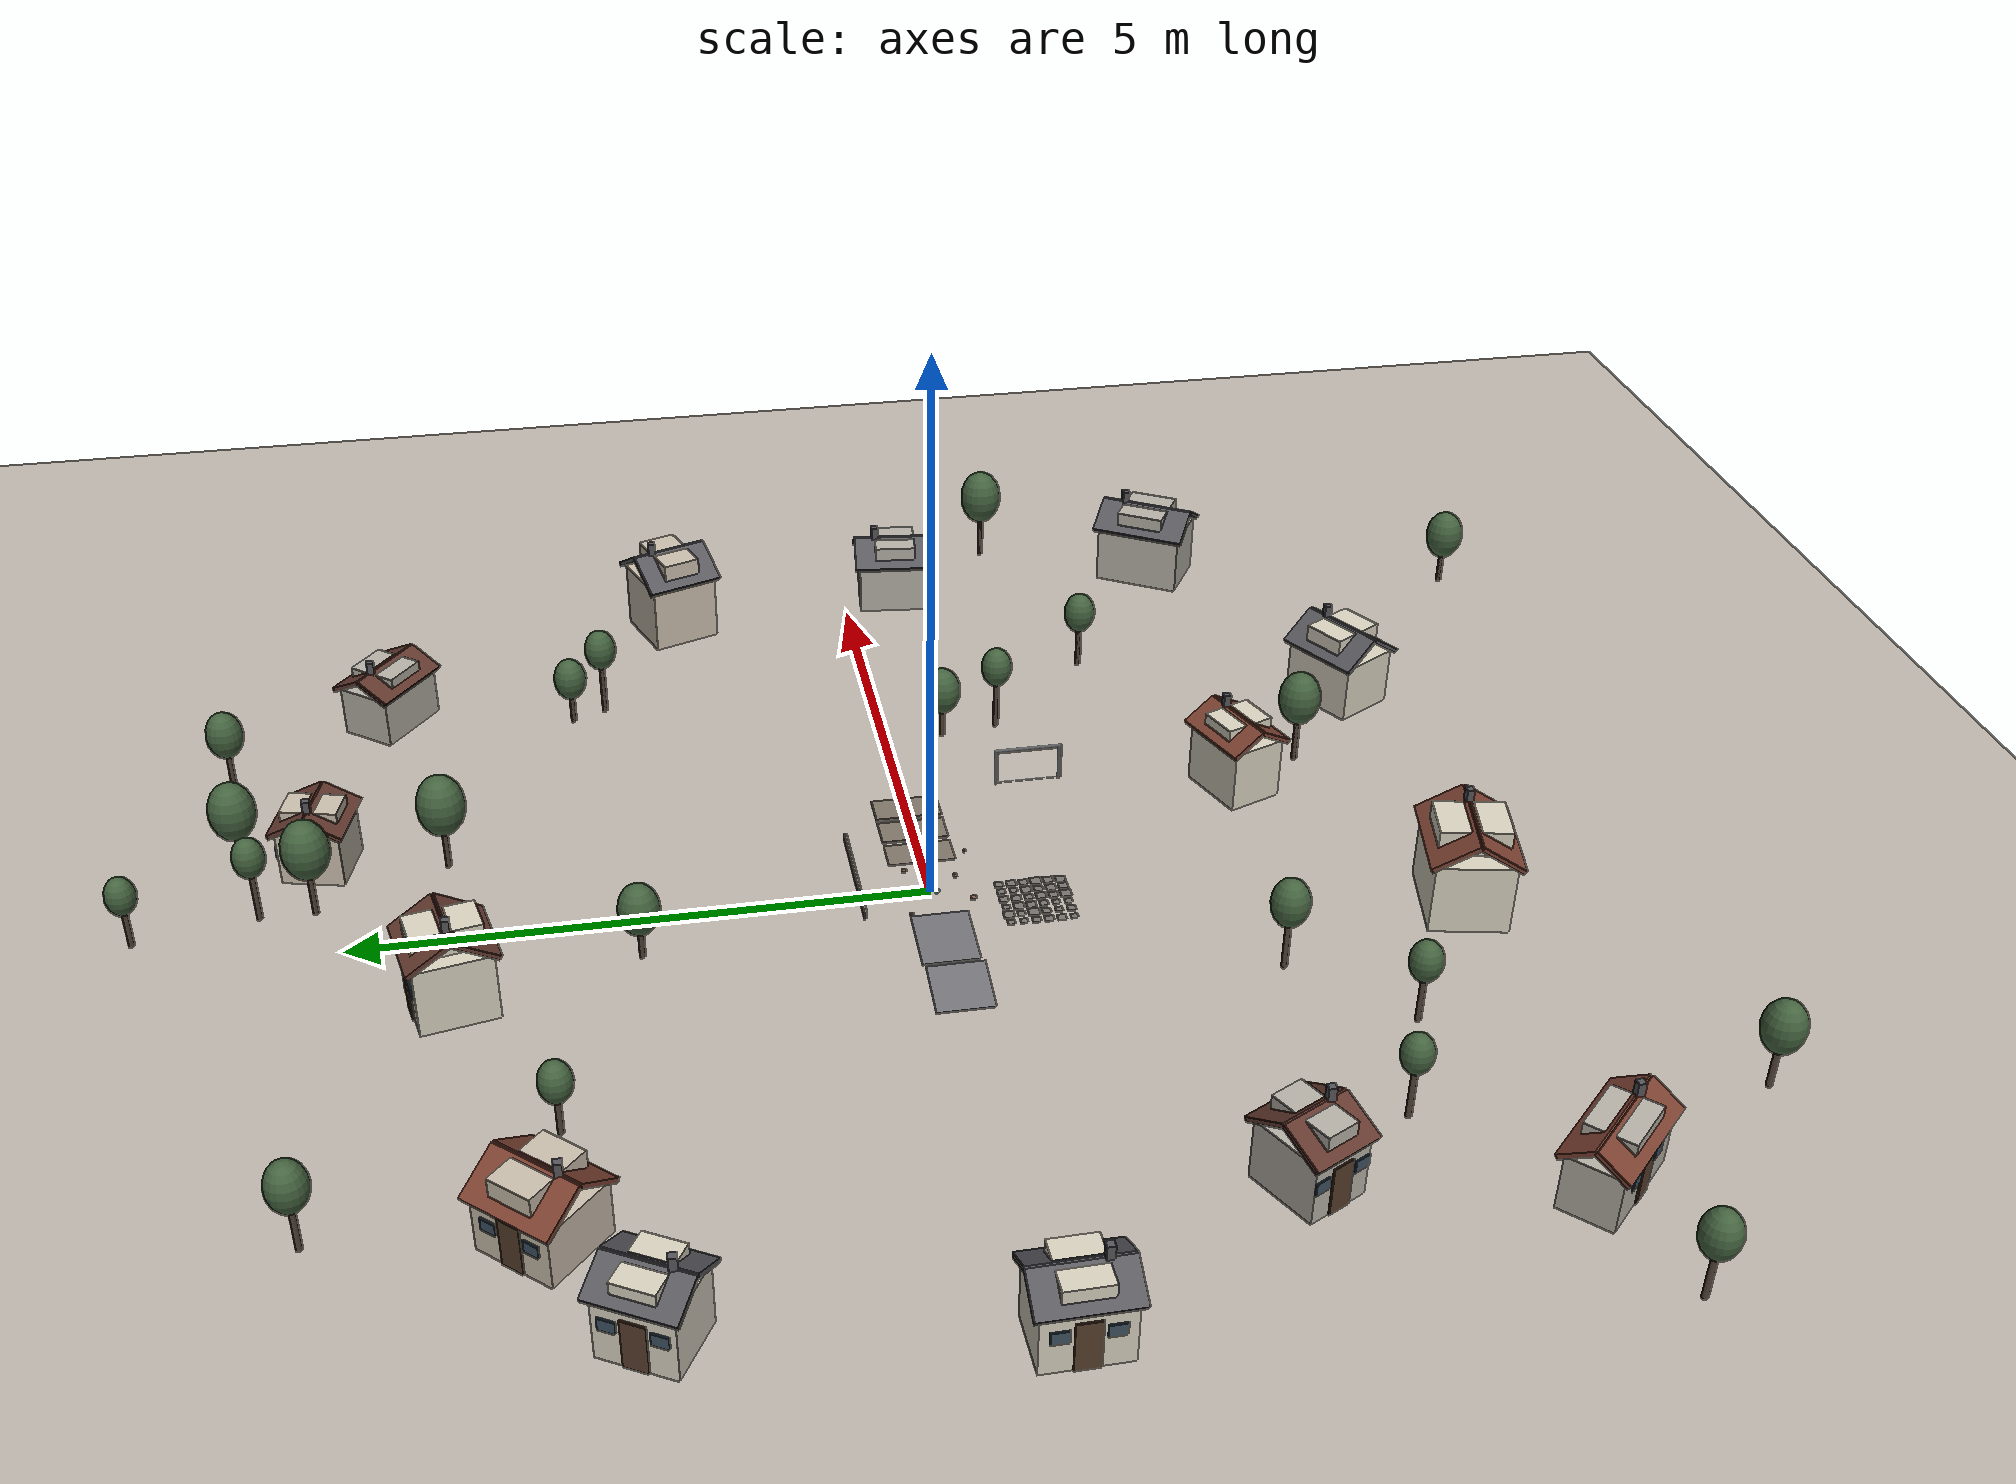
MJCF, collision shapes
<mujoco model="scene_obstacles">
    <include file="robot_allcollisions_cam.xml" />
    <!-- 70mm / 15g ball — the same body the kick policies were trained on.
         Its freejoint adds 7 qpos, so every keyframe below is extended to match. -->
    <include file="ball.xml" />

    <visual>
        <!-- Softer key light + real ambient, so shading comes from the scene lights
             rather than a flat headlight washing everything out. -->
        <headlight diffuse="0.25 0.25 0.25" ambient="0.22 0.22 0.24" specular="0.05 0.05 0.05" />
        <rgba haze="0.78 0.83 0.89 1" />
        <global azimuth="140" elevation="-22" offwidth="1920" offheight="1080" />
        <quality shadowsize="8192" offsamples="8" />
        <map fogstart="14" fogend="55" shadowclip="3" shadowscale="1.2" />
    </visual>

    <asset>
        <texture type="skybox" name="sky"
            fileright="sky_right.png" fileleft="sky_left.png"
            filefront="sky_front.png" fileback="sky_back.png"
            fileup="sky_up.png"       filedown="sky_down.png" />
        <!-- Real concrete: seamless 1024px texture generated by make_ground_texture.py.
             FFT-filtered noise is periodic, so it tiles with no visible seam. -->
        <texture type="2d" name="groundplane" file="ground_concrete.png" />
        <!-- texrepeat 0.6 => one 1024px tile per ~1.7 m, so the duck (0.25 m) sees
             fine aggregate rather than a repeating pattern. -->
        <material name="groundplane" texture="groundplane" texuniform="true" texrepeat="0.6 0.6"
            reflectance="0.02" specular="0.12" shininess="0.08" />
        <!-- Village palette: plaster walls, terracotta/slate roofs. -->
        <material name="wall0" rgba="0.86 0.83 0.76 1" specular="0.10" shininess="0.05"/>
        <material name="wall1" rgba="0.80 0.75 0.68 1" specular="0.10" shininess="0.05"/>
        <material name="wall2" rgba="0.72 0.70 0.66 1" specular="0.10" shininess="0.05"/>
        <material name="roof0" rgba="0.48 0.25 0.19 1" specular="0.18" shininess="0.12"/>
        <material name="roof1" rgba="0.38 0.22 0.18 1" specular="0.18" shininess="0.12"/>
        <material name="roof2" rgba="0.34 0.34 0.36 1" specular="0.18" shininess="0.12"/>
        <material name="door"  rgba="0.34 0.24 0.17 1" specular="0.20" shininess="0.15"/>
        <material name="glass" rgba="0.24 0.32 0.38 1" specular="0.85" shininess="0.75"
                  reflectance="0.25"/>
        <material name="bark"  rgba="0.31 0.25 0.20 1" specular="0.06"/>
        <material name="leaf"  rgba="0.26 0.38 0.24 1" specular="0.10" shininess="0.06"/>
        <material name="goal" rgba="0.92 0.93 0.95 1" specular="0.4" shininess="0.3"/>
        <material name="goalline" rgba="0.95 0.95 0.96 1"/>
        <material name="obstacle" rgba="0.50 0.46 0.41 1" reflectance="0.02" specular="0.15" shininess="0.1"/>
        <material name="ramp"     rgba="0.44 0.44 0.46 1" reflectance="0.02" specular="0.15" shininess="0.1"/>
        <material name="debris"   rgba="0.52 0.40 0.34 1" reflectance="0.02" specular="0.15" shininess="0.1"/>
        <material name="rough"    rgba="0.47 0.45 0.43 1" reflectance="0.02" specular="0.12" shininess="0.08"/>
    </asset>

    <worldbody>
        <!-- Key light is angled, not straight down: shadows are what make the
             obstacle heights readable at a glance. Fill lifts the shadow side. -->
        <light name="key"  pos="1.8 -2.2 3.0" dir="-0.45 0.55 -0.75" directional="true"
               diffuse="0.85 0.83 0.78" specular="0.25 0.25 0.25" castshadow="true" />
        <light name="fill" pos="-2.5 2.0 2.0" dir="0.6 -0.5 -0.62" directional="true"
               diffuse="0.22 0.24 0.28" specular="0 0 0" castshadow="false" />
        <geom name="floor" size="0 0 0.05" pos="0 0 0" type="plane" material="groundplane" />

        <!-- VILLAGE:BEGIN -->
        <!-- house 0 -->
        <geom name="v0_body" type="box" size="0.368 0.271 0.250" pos="5.284 -0.545 0.250" quat="0.742482 0.000000 0.000000 0.669866" material="wall2"/>
        <geom name="v0_roofa" type="box" size="0.413 0.189 0.022" pos="5.126 -0.529 0.603" quat="0.711680 -0.211640 -0.190941 0.642076" material="roof2"/>
        <geom name="v0_roofb" type="box" size="0.413 0.189 0.022" pos="5.441 -0.561 0.603" quat="0.711680 0.211640 0.190941 0.642076" material="roof2"/>
        <geom name="v0_gable" type="box" size="0.203 0.244 0.103" pos="5.284 -0.545 0.603" quat="0.742482 0.000000 0.000000 0.669866" material="wall2"/>
        <geom name="v0_door" type="box" size="0.100 0.008 0.220" pos="5.560 -0.573 0.220" quat="0.742482 0.000000 0.000000 0.669866" material="door"/>
        <geom name="v0_winl" type="box" size="0.070 0.008 0.055" pos="5.580 -0.374 0.310" quat="0.742482 0.000000 0.000000 0.669866" material="glass"/>
        <geom name="v0_winr" type="box" size="0.070 0.008 0.055" pos="5.539 -0.772 0.310" quat="0.742482 0.000000 0.000000 0.669866" material="glass"/>
        <geom name="v0_chim" type="box" size="0.032 0.032 0.09" pos="5.305 -0.340 0.746" material="roof2"/>
        <!-- house 1 -->
        <geom name="v1_body" type="box" size="0.335 0.346 0.329" pos="5.038 1.814 0.329" quat="0.575015 0.000000 0.000000 0.818143" material="wall1"/>
        <geom name="v1_roofa" type="box" size="0.380 0.229 0.022" pos="4.854 1.747 0.777" quat="0.553629 -0.155361 -0.221051 0.787715" material="roof2"/>
        <geom name="v1_roofb" type="box" size="0.380 0.229 0.022" pos="5.222 1.880 0.777" quat="0.553629 0.155361 0.221051 0.787715" material="roof2"/>
        <geom name="v1_gable" type="box" size="0.184 0.311 0.119" pos="5.038 1.814 0.777" quat="0.575015 0.000000 0.000000 0.818143" material="wall1"/>
        <geom name="v1_door" type="box" size="0.100 0.008 0.220" pos="5.369 1.933 0.220" quat="0.575015 0.000000 0.000000 0.818143" material="door"/>
        <geom name="v1_winl" type="box" size="0.070 0.008 0.055" pos="5.301 2.121 0.408" quat="0.575015 0.000000 0.000000 0.818143" material="glass"/>
        <geom name="v1_winr" type="box" size="0.070 0.008 0.055" pos="5.437 1.745 0.408" quat="0.575015 0.000000 0.000000 0.818143" material="glass"/>
        <geom name="v1_chim" type="box" size="0.032 0.032 0.09" pos="4.974 1.990 0.936" material="roof2"/>
        <!-- house 2 -->
        <geom name="v2_body" type="box" size="0.365 0.267 0.239" pos="3.672 4.651 0.239" quat="0.327990 0.000000 0.000000 0.944681" material="wall2"/>
        <geom name="v2_roofa" type="box" size="0.410 0.175 0.022" pos="3.575 4.528 0.556" quat="0.319154 -0.075615 -0.217787 0.919234" material="roof1"/>
        <geom name="v2_roofb" type="box" size="0.410 0.175 0.022" pos="3.769 4.773 0.556" quat="0.319154 0.075615 0.217787 0.919234" material="roof1"/>
        <geom name="v2_gable" type="box" size="0.201 0.241 0.078" pos="3.672 4.651 0.556" quat="0.327990 0.000000 0.000000 0.944681" material="wall2"/>
        <geom name="v2_door" type="box" size="0.100 0.008 0.220" pos="3.841 4.865 0.220" quat="0.327990 0.000000 0.000000 0.944681" material="door"/>
        <geom name="v2_winl" type="box" size="0.070 0.008 0.055" pos="3.684 4.989 0.296" quat="0.327990 0.000000 0.000000 0.944681" material="glass"/>
        <geom name="v2_winr" type="box" size="0.070 0.008 0.055" pos="3.998 4.741 0.296" quat="0.327990 0.000000 0.000000 0.944681" material="glass"/>
        <geom name="v2_chim" type="box" size="0.032 0.032 0.09" pos="3.512 4.777 0.675" material="roof2"/>
        <!-- house 3 -->
        <geom name="v3_body" type="box" size="0.278 0.281 0.251" pos="1.315 5.226 0.251" quat="0.122942 0.000000 0.000000 0.992414" material="wall1"/>
        <geom name="v3_roofa" type="box" size="0.323 0.182 0.022" pos="1.275 5.068 0.583" quat="0.119717 -0.027973 -0.225803 0.966384" material="roof1"/>
        <geom name="v3_roofb" type="box" size="0.323 0.182 0.022" pos="1.355 5.384 0.583" quat="0.119717 0.027973 0.225803 0.966384" material="roof1"/>
        <geom name="v3_gable" type="box" size="0.153 0.253 0.081" pos="1.315 5.226 0.583" quat="0.122942 0.000000 0.000000 0.992414" material="wall1"/>
        <geom name="v3_door" type="box" size="0.100 0.008 0.220" pos="1.385 5.504 0.220" quat="0.122942 0.000000 0.000000 0.992414" material="door"/>
        <geom name="v3_winl" type="box" size="0.070 0.008 0.055" pos="1.191 5.553 0.311" quat="0.122942 0.000000 0.000000 0.992414" material="glass"/>
        <geom name="v3_winr" type="box" size="0.070 0.008 0.055" pos="1.579 5.455 0.311" quat="0.122942 0.000000 0.000000 0.992414" material="glass"/>
        <geom name="v3_chim" type="box" size="0.032 0.032 0.09" pos="1.164 5.264 0.703" material="roof2"/>
        <!-- house 4 -->
        <geom name="v4_body" type="box" size="0.317 0.334 0.312" pos="-0.848 4.103 0.312" quat="0.101674 0.000000 -0.000000 -0.994818" material="wall0"/>
        <geom name="v4_roofa" type="box" size="0.362 0.221 0.022" pos="-0.809 3.918 0.737" quat="0.097972 -0.027185 0.265992 -0.958598" material="roof1"/>
        <geom name="v4_roofb" type="box" size="0.362 0.221 0.022" pos="-0.886 4.289 0.737" quat="0.097972 0.027185 -0.265992 -0.958598" material="roof1"/>
        <geom name="v4_gable" type="box" size="0.174 0.301 0.114" pos="-0.848 4.103 0.737" quat="0.101674 0.000000 -0.000000 -0.994818" material="wall0"/>
        <geom name="v4_door" type="box" size="0.100 0.008 0.220" pos="-0.916 4.437 0.220" quat="0.101674 0.000000 -0.000000 -0.994818" material="door"/>
        <geom name="v4_winl" type="box" size="0.070 0.008 0.055" pos="-1.112 4.396 0.386" quat="0.101674 0.000000 -0.000000 -0.994818" material="glass"/>
        <geom name="v4_winr" type="box" size="0.070 0.008 0.055" pos="-0.721 4.477 0.386" quat="0.101674 0.000000 -0.000000 -0.994818" material="glass"/>
        <geom name="v4_chim" type="box" size="0.032 0.032 0.09" pos="-1.021 4.067 0.891" material="roof2"/>
        <!-- house 5 -->
        <geom name="v5_body" type="box" size="0.362 0.338 0.245" pos="-3.686 3.466 0.245" quat="0.396857 0.000000 -0.000000 -0.917880" material="wall1"/>
        <geom name="v5_roofa" type="box" size="0.407 0.226 0.022" pos="-3.546 3.335 0.609" quat="0.381446 -0.109521 0.253308 -0.882235" material="roof0"/>
        <geom name="v5_roofb" type="box" size="0.407 0.226 0.022" pos="-3.825 3.597 0.609" quat="0.381446 0.109521 -0.253308 -0.882235" material="roof0"/>
        <geom name="v5_gable" type="box" size="0.199 0.304 0.120" pos="-3.686 3.466 0.609" quat="0.396857 0.000000 -0.000000 -0.917880" material="wall1"/>
        <geom name="v5_door" type="box" size="0.100 0.008 0.220" pos="-3.936 3.701 0.220" quat="0.396857 0.000000 -0.000000 -0.917880" material="door"/>
        <geom name="v5_winl" type="box" size="0.070 0.008 0.055" pos="-4.073 3.555 0.303" quat="0.396857 0.000000 -0.000000 -0.917880" material="glass"/>
        <geom name="v5_winr" type="box" size="0.070 0.008 0.055" pos="-3.799 3.847 0.303" quat="0.396857 0.000000 -0.000000 -0.917880" material="glass"/>
        <geom name="v5_chim" type="box" size="0.032 0.032 0.09" pos="-3.824 3.318 0.769" material="roof2"/>
        <!-- house 6 -->
        <geom name="v6_body" type="box" size="0.321 0.287 0.281" pos="-4.770 2.764 0.281" quat="0.499349 0.000000 -0.000000 -0.866401" material="wall0"/>
        <geom name="v6_roofa" type="box" size="0.366 0.185 0.022" pos="-4.627 2.680 0.644" quat="0.486325 -0.113301 0.196584 -0.843804" material="roof2"/>
        <geom name="v6_roofb" type="box" size="0.366 0.185 0.022" pos="-4.914 2.847 0.644" quat="0.486325 0.113301 -0.196584 -0.843804" material="roof2"/>
        <geom name="v6_gable" type="box" size="0.176 0.258 0.082" pos="-4.770 2.764 0.644" quat="0.499349 0.000000 -0.000000 -0.866401" material="wall0"/>
        <geom name="v6_door" type="box" size="0.100 0.008 0.220" pos="-5.023 2.910 0.220" quat="0.499349 0.000000 -0.000000 -0.866401" material="door"/>
        <geom name="v6_winl" type="box" size="0.070 0.008 0.055" pos="-5.124 2.737 0.349" quat="0.499349 0.000000 -0.000000 -0.866401" material="glass"/>
        <geom name="v6_winr" type="box" size="0.070 0.008 0.055" pos="-4.923 3.083 0.349" quat="0.499349 0.000000 -0.000000 -0.866401" material="glass"/>
        <geom name="v6_chim" type="box" size="0.032 0.032 0.09" pos="-4.860 2.608 0.766" material="roof2"/>
        <!-- house 7 -->
        <geom name="v7_body" type="box" size="0.349 0.278 0.269" pos="-5.250 -0.081 0.269" quat="0.712571 0.000000 -0.000000 -0.701600" material="wall0"/>
        <geom name="v7_roofa" type="box" size="0.394 0.185 0.022" pos="-5.089 -0.079 0.630" quat="0.689168 -0.181119 0.178331 -0.678558" material="roof2"/>
        <geom name="v7_roofb" type="box" size="0.394 0.185 0.022" pos="-5.412 -0.084 0.630" quat="0.689168 0.181119 -0.178331 -0.678558" material="roof2"/>
        <geom name="v7_gable" type="box" size="0.192 0.250 0.091" pos="-5.250 -0.081 0.630" quat="0.712571 0.000000 -0.000000 -0.701600" material="wall0"/>
        <geom name="v7_door" type="box" size="0.100 0.008 0.220" pos="-5.534 -0.086 0.220" quat="0.712571 0.000000 -0.000000 -0.701600" material="door"/>
        <geom name="v7_winl" type="box" size="0.070 0.008 0.055" pos="-5.531 -0.286 0.334" quat="0.712571 0.000000 -0.000000 -0.701600" material="glass"/>
        <geom name="v7_winr" type="box" size="0.070 0.008 0.055" pos="-5.537 0.114 0.334" quat="0.712571 0.000000 -0.000000 -0.701600" material="glass"/>
        <geom name="v7_chim" type="box" size="0.032 0.032 0.09" pos="-5.247 -0.277 0.761" material="roof2"/>
        <!-- house 8 -->
        <geom name="v8_body" type="box" size="0.275 0.324 0.273" pos="-4.070 -2.086 0.273" quat="0.853229 0.000000 -0.000000 -0.521536" material="wall2"/>
        <geom name="v8_roofa" type="box" size="0.320 0.209 0.022" pos="-3.906 -2.001 0.643" quat="0.828233 -0.205014 0.125315 -0.506257" material="roof1"/>
        <geom name="v8_roofb" type="box" size="0.320 0.209 0.022" pos="-4.235 -2.170 0.643" quat="0.828233 0.205014 -0.125315 -0.506257" material="roof1"/>
        <geom name="v8_gable" type="box" size="0.151 0.292 0.097" pos="-4.070 -2.086 0.643" quat="0.853229 0.000000 -0.000000 -0.521536" material="wall2"/>
        <geom name="v8_door" type="box" size="0.100 0.008 0.220" pos="-4.364 -2.236 0.220" quat="0.853229 0.000000 -0.000000 -0.521536" material="door"/>
        <geom name="v8_winl" type="box" size="0.070 0.008 0.055" pos="-4.273 -2.414 0.338" quat="0.853229 0.000000 -0.000000 -0.521536" material="glass"/>
        <geom name="v8_winr" type="box" size="0.070 0.008 0.055" pos="-4.456 -2.058 0.338" quat="0.853229 0.000000 -0.000000 -0.521536" material="glass"/>
        <geom name="v8_chim" type="box" size="0.032 0.032 0.09" pos="-4.000 -2.223 0.780" material="roof2"/>
        <!-- house 9 -->
        <geom name="v9_body" type="box" size="0.473 0.232 0.250" pos="-4.451 -4.295 0.250" quat="0.920418 0.000000 -0.000000 -0.390936" material="wall2"/>
        <geom name="v9_roofa" type="box" size="0.518 0.164 0.022" pos="-4.352 -4.199 0.588" quat="0.883804 -0.257021 0.109166 -0.375384" material="roof0"/>
        <geom name="v9_roofb" type="box" size="0.518 0.164 0.022" pos="-4.551 -4.391 0.588" quat="0.883804 0.257021 -0.109166 -0.375384" material="roof0"/>
        <geom name="v9_gable" type="box" size="0.260 0.209 0.088" pos="-4.451 -4.295 0.588" quat="0.920418 0.000000 -0.000000 -0.390936" material="wall2"/>
        <geom name="v9_door" type="box" size="0.100 0.008 0.220" pos="-4.623 -4.460 0.220" quat="0.920418 0.000000 -0.000000 -0.390936" material="door"/>
        <geom name="v9_winl" type="box" size="0.070 0.008 0.055" pos="-4.484 -4.604 0.310" quat="0.920418 0.000000 -0.000000 -0.390936" material="glass"/>
        <geom name="v9_winr" type="box" size="0.070 0.008 0.055" pos="-4.762 -4.316 0.310" quat="0.920418 0.000000 -0.000000 -0.390936" material="glass"/>
        <geom name="v9_chim" type="box" size="0.032 0.032 0.09" pos="-4.268 -4.485 0.717" material="roof2"/>
        <!-- house 10 -->
        <geom name="v10_body" type="box" size="0.430 0.345 0.324" pos="-0.922 -4.481 0.324" quat="0.994856 0.000000 -0.000000 -0.101298" material="wall0"/>
        <geom name="v10_roofa" type="box" size="0.475 0.228 0.022" pos="-0.883 -4.290 0.767" quat="0.958256 -0.267366 0.027224 -0.097571" material="roof0"/>
        <geom name="v10_roofb" type="box" size="0.475 0.228 0.022" pos="-0.961 -4.672 0.767" quat="0.958256 0.267366 -0.027224 -0.097571" material="roof0"/>
        <geom name="v10_gable" type="box" size="0.236 0.310 0.118" pos="-0.922 -4.481 0.767" quat="0.994856 0.000000 -0.000000 -0.101298" material="wall0"/>
        <geom name="v10_door" type="box" size="0.100 0.008 0.220" pos="-0.993 -4.824 0.220" quat="0.994856 0.000000 -0.000000 -0.101298" material="door"/>
        <geom name="v10_winl" type="box" size="0.070 0.008 0.055" pos="-0.797 -4.865 0.402" quat="0.994856 0.000000 -0.000000 -0.101298" material="glass"/>
        <geom name="v10_winr" type="box" size="0.070 0.008 0.055" pos="-1.189 -4.784 0.402" quat="0.994856 0.000000 -0.000000 -0.101298" material="glass"/>
        <geom name="v10_chim" type="box" size="0.032 0.032 0.09" pos="-0.686 -4.529 0.925" material="roof2"/>
        <!-- house 11 -->
        <geom name="v11_body" type="box" size="0.335 0.260 0.294" pos="1.178 -3.059 0.294" quat="0.983169 0.000000 0.000000 0.182698" material="wall0"/>
        <geom name="v11_roofa" type="box" size="0.380 0.176 0.022" pos="1.123 -2.917 0.675" quat="0.950443 -0.251553 -0.046745 0.176616" material="roof0"/>
        <geom name="v11_roofb" type="box" size="0.380 0.176 0.022" pos="1.232 -3.202 0.675" quat="0.950443 0.251553 0.046745 0.176616" material="roof0"/>
        <geom name="v11_gable" type="box" size="0.184 0.234 0.087" pos="1.178 -3.059 0.675" quat="0.983169 0.000000 0.000000 0.182698" material="wall0"/>
        <geom name="v11_door" type="box" size="0.100 0.008 0.220" pos="1.273 -3.308 0.220" quat="0.983169 0.000000 0.000000 0.182698" material="door"/>
        <geom name="v11_winl" type="box" size="0.070 0.008 0.055" pos="1.460 -3.236 0.365" quat="0.983169 0.000000 0.000000 0.182698" material="glass"/>
        <geom name="v11_winr" type="box" size="0.070 0.008 0.055" pos="1.087 -3.379 0.365" quat="0.983169 0.000000 0.000000 0.182698" material="glass"/>
        <geom name="v11_chim" type="box" size="0.032 0.032 0.09" pos="1.352 -2.992 0.802" material="roof2"/>
        <!-- house 12 -->
        <geom name="v12_body" type="box" size="0.373 0.300 0.279" pos="2.569 -4.515 0.279" quat="0.966735 0.000000 0.000000 0.255782" material="wall0"/>
        <geom name="v12_roofa" type="box" size="0.418 0.209 0.022" pos="2.483 -4.365 0.676" quat="0.923829 -0.284808 -0.075356 0.244430" material="roof2"/>
        <geom name="v12_roofb" type="box" size="0.418 0.209 0.022" pos="2.654 -4.665 0.676" quat="0.923829 0.284808 0.075356 0.244430" material="roof2"/>
        <geom name="v12_gable" type="box" size="0.205 0.270 0.118" pos="2.569 -4.515 0.676" quat="0.966735 0.000000 0.000000 0.255782" material="wall0"/>
        <geom name="v12_door" type="box" size="0.100 0.008 0.220" pos="2.720 -4.781 0.220" quat="0.966735 0.000000 0.000000 0.255782" material="door"/>
        <geom name="v12_winl" type="box" size="0.070 0.008 0.055" pos="2.894 -4.682 0.346" quat="0.966735 0.000000 0.000000 0.255782" material="glass"/>
        <geom name="v12_winr" type="box" size="0.070 0.008 0.055" pos="2.546 -4.880 0.346" quat="0.966735 0.000000 0.000000 0.255782" material="glass"/>
        <geom name="v12_chim" type="box" size="0.032 0.032 0.09" pos="2.750 -4.411 0.833" material="roof2"/>
        <!-- house 13 -->
        <geom name="v13_body" type="box" size="0.433 0.305 0.292" pos="5.383 -3.290 0.292" quat="0.872197 0.000000 0.000000 0.489154" material="wall2"/>
        <geom name="v13_roofa" type="box" size="0.478 0.203 0.022" pos="5.234 -3.199 0.687" quat="0.841841 -0.228105 -0.127928 0.472130" material="roof2"/>
        <geom name="v13_roofb" type="box" size="0.478 0.203 0.022" pos="5.533 -3.381 0.687" quat="0.841841 0.228105 0.127928 0.472130" material="roof2"/>
        <geom name="v13_gable" type="box" size="0.238 0.274 0.102" pos="5.383 -3.290 0.687" quat="0.872197 0.000000 0.000000 0.489154" material="wall2"/>
        <geom name="v13_door" type="box" size="0.100 0.008 0.220" pos="5.649 -3.452 0.220" quat="0.872197 0.000000 0.000000 0.489154" material="door"/>
        <geom name="v13_winl" type="box" size="0.070 0.008 0.055" pos="5.753 -3.281 0.363" quat="0.872197 0.000000 0.000000 0.489154" material="glass"/>
        <geom name="v13_winr" type="box" size="0.070 0.008 0.055" pos="5.544 -3.623 0.363" quat="0.872197 0.000000 0.000000 0.489154" material="glass"/>
        <geom name="v13_chim" type="box" size="0.032 0.032 0.09" pos="5.510 -3.083 0.829" material="roof2"/>
        <geom name="t0_trunk" type="cylinder" size="0.026 0.252" pos="0.604 5.724 0.252" material="bark"/>
        <geom name="t0_top" type="ellipsoid" size="0.142 0.142 0.192" pos="0.604 5.724 0.639" material="leaf"/>
        <geom name="t1_trunk" type="cylinder" size="0.026 0.246" pos="-3.483 -3.090 0.246" material="bark"/>
        <geom name="t1_top" type="ellipsoid" size="0.136 0.136 0.184" pos="-3.483 -3.090 0.621" material="leaf"/>
        <geom name="t2_trunk" type="cylinder" size="0.026 0.229" pos="-5.638 -4.477 0.229" material="bark"/>
        <geom name="t2_top" type="ellipsoid" size="0.159 0.159 0.215" pos="-5.638 -4.477 0.608" material="leaf"/>
        <geom name="t3_trunk" type="cylinder" size="0.026 0.234" pos="-2.396 -3.563 0.234" material="bark"/>
        <geom name="t3_top" type="ellipsoid" size="0.142 0.142 0.191" pos="-2.396 -3.563 0.602" material="leaf"/>
        <geom name="t4_trunk" type="cylinder" size="0.026 0.160" pos="-0.484 2.537 0.160" material="bark"/>
        <geom name="t4_top" type="ellipsoid" size="0.180 0.180 0.243" pos="-0.484 2.537 0.492" material="leaf"/>
        <geom name="t5_trunk" type="cylinder" size="0.026 0.232" pos="0.607 5.255 0.232" material="bark"/>
        <geom name="t5_top" type="ellipsoid" size="0.209 0.209 0.283" pos="0.607 5.255 0.664" material="leaf"/>
        <geom name="t6_trunk" type="cylinder" size="0.026 0.189" pos="-2.566 3.306 0.189" material="bark"/>
        <geom name="t6_top" type="ellipsoid" size="0.141 0.141 0.190" pos="-2.566 3.306 0.512" material="leaf"/>
        <geom name="t7_trunk" type="cylinder" size="0.026 0.209" pos="-3.627 -5.976 0.209" material="bark"/>
        <geom name="t7_top" type="ellipsoid" size="0.180 0.180 0.243" pos="-3.627 -5.976 0.589" material="leaf"/>
        <geom name="t8_trunk" type="cylinder" size="0.026 0.243" pos="6.100 -1.629 0.243" material="bark"/>
        <geom name="t8_top" type="ellipsoid" size="0.210 0.210 0.284" pos="6.100 -1.629 0.686" material="leaf"/>
        <geom name="t9_trunk" type="cylinder" size="0.026 0.240" pos="1.288 5.902 0.240" material="bark"/>
        <geom name="t9_top" type="ellipsoid" size="0.206 0.206 0.278" pos="1.288 5.902 0.675" material="leaf"/>
        <geom name="t10_trunk" type="cylinder" size="0.026 0.226" pos="-3.478 5.202 0.226" material="bark"/>
        <geom name="t10_top" type="ellipsoid" size="0.167 0.167 0.225" pos="-3.478 5.202 0.610" material="leaf"/>
        <geom name="t11_trunk" type="cylinder" size="0.026 0.270" pos="3.514 2.610 0.270" material="bark"/>
        <geom name="t11_top" type="ellipsoid" size="0.149 0.149 0.202" pos="3.514 2.610 0.683" material="leaf"/>
        <geom name="t12_trunk" type="cylinder" size="0.026 0.163" pos="3.370 2.920 0.163" material="bark"/>
        <geom name="t12_top" type="ellipsoid" size="0.154 0.154 0.208" pos="3.370 2.920 0.472" material="leaf"/>
        <geom name="t13_trunk" type="cylinder" size="0.026 0.223" pos="3.595 -2.143 0.223" material="bark"/>
        <geom name="t13_top" type="ellipsoid" size="0.151 0.151 0.205" pos="3.595 -2.143 0.590" material="leaf"/>
        <geom name="t14_trunk" type="cylinder" size="0.026 0.249" pos="-1.535 -2.710 0.249" material="bark"/>
        <geom name="t14_top" type="ellipsoid" size="0.168 0.168 0.227" pos="-1.535 -2.710 0.657" material="leaf"/>
        <geom name="t15_trunk" type="cylinder" size="0.026 0.219" pos="2.691 6.077 0.219" material="bark"/>
        <geom name="t15_top" type="ellipsoid" size="0.169 0.169 0.229" pos="2.691 6.077 0.600" material="leaf"/>
        <geom name="t16_trunk" type="cylinder" size="0.026 0.196" pos="0.399 6.764 0.196" material="bark"/>
        <geom name="t16_top" type="ellipsoid" size="0.134 0.134 0.181" pos="0.399 6.764 0.519" material="leaf"/>
        <geom name="t17_trunk" type="cylinder" size="0.026 0.165" pos="2.510 -0.555 0.165" material="bark"/>
        <geom name="t17_top" type="ellipsoid" size="0.172 0.172 0.232" pos="2.510 -0.555 0.493" material="leaf"/>
        <geom name="t18_trunk" type="cylinder" size="0.026 0.221" pos="1.119 4.128 0.221" material="bark"/>
        <geom name="t18_top" type="ellipsoid" size="0.216 0.216 0.292" pos="1.119 4.128 0.647" material="leaf"/>
        <geom name="t19_trunk" type="cylinder" size="0.026 0.257" pos="2.592 -1.096 0.257" material="bark"/>
        <geom name="t19_top" type="ellipsoid" size="0.145 0.145 0.196" pos="2.592 -1.096 0.651" material="leaf"/>
        <geom name="t20_trunk" type="cylinder" size="0.026 0.240" pos="1.528 -3.761 0.240" material="bark"/>
        <geom name="t20_top" type="ellipsoid" size="0.195 0.195 0.263" pos="1.528 -3.761 0.664" material="leaf"/>
        <geom name="t21_trunk" type="cylinder" size="0.026 0.184" pos="4.657 -6.364 0.184" material="bark"/>
        <geom name="t21_top" type="ellipsoid" size="0.187 0.187 0.252" pos="4.657 -6.364 0.546" material="leaf"/>
        <!-- VILLAGE:END -->

        <!-- Goal, 60cm wide. Static geoms — a goal the duck could knock over
             would be a physics toy, not a target. -->
        <geom name="goal_post_l" type="capsule" size="0.016" material="goal"
              fromto="1.60 -0.90 0 1.60 -0.90 0.34"/>
        <geom name="goal_post_r" type="capsule" size="0.016" material="goal"
              fromto="1.60 -1.50 0 1.60 -1.50 0.34"/>
        <geom name="goal_bar"    type="capsule" size="0.016" material="goal"
              fromto="1.60 -0.90 0.34 1.60 -1.50 0.34"/>
        <geom name="goal_line"   type="box" size="0.005 0.30 0.001" pos="1.60 -1.20 0.001"
              material="goalline"/>

        <!-- Low steps: a staircase of increasing difficulty going +X -->
        <geom name="step1" type="box" size="0.15 0.30 0.004" pos="0.6 0 0.004" material="obstacle"/>
        <geom name="step2" type="box" size="0.15 0.30 0.008" pos="0.95 0 0.008" material="obstacle"/>
        <geom name="step3" type="box" size="0.15 0.30 0.013" pos="1.30 0 0.013" material="obstacle"/>

        <!-- Ramps: gentle then steep, going -X -->
        <geom name="ramp_gentle" type="box" size="0.30 0.25 0.005" pos="-0.7 0 0.03"
              euler="0 -0.10 0" material="ramp"/>
        <geom name="ramp_steep"  type="box" size="0.25 0.25 0.005" pos="-1.4 0 0.05"
              euler="0 -0.20 0" material="ramp"/>

        <!-- Scattered debris: small blocks it has to step over or around -->
        <geom name="deb1" type="box" size="0.02 0.02 0.006" pos="0.35 0.18 0.006" material="debris"/>
        <geom name="deb2" type="box" size="0.03 0.015 0.005" pos="0.20 -0.25 0.005" material="debris"/>
        <geom name="deb3" type="cylinder" size="0.018 0.008" pos="-0.30 0.22 0.008" material="debris"/>
        <geom name="deb4" type="box" size="0.025 0.025 0.007" pos="-0.15 -0.35 0.007" material="debris"/>
        <geom name="deb5" type="cylinder" size="0.012 0.010" pos="0.55 -0.40 0.010" material="debris"/>

        <!-- A low wall to walk along / turn at -->
        <geom name="wall_y" type="box" size="0.60 0.012 0.040" pos="0.3 0.62 0.040" material="obstacle"/>

        <!-- Rough patch: a grid of small random bumps (the hard one) -->
        <geom name="bump0" type="box" size="0.033 0.033 0.003" pos="-0.55 -0.6 0.003" material="rough"/>
        <geom name="bump1" type="box" size="0.031 0.031 0.0044" pos="-0.55 -0.71 0.0044" material="rough"/>
        <geom name="bump2" type="box" size="0.037 0.037 0.0039" pos="-0.55 -0.82 0.0039" material="rough"/>
        <geom name="bump3" type="box" size="0.04 0.04 0.0018" pos="-0.55 -0.93 0.0018" material="rough"/>
        <geom name="bump4" type="box" size="0.039 0.039 0.0017" pos="-0.55 -1.04 0.0017" material="rough"/>
        <geom name="bump5" type="box" size="0.032 0.032 0.0018" pos="-0.55 -1.15 0.0018" material="rough"/>
        <geom name="bump6" type="box" size="0.047 0.047 0.0034" pos="-0.44 -0.6 0.0034" material="rough"/>
        <geom name="bump7" type="box" size="0.034 0.034 0.0021" pos="-0.44 -0.71 0.0021" material="rough"/>
        <geom name="bump8" type="box" size="0.049 0.049 0.0043" pos="-0.44 -0.82 0.0043" material="rough"/>
        <geom name="bump9" type="box" size="0.038 0.038 0.0041" pos="-0.44 -0.93 0.0041" material="rough"/>
        <geom name="bump10" type="box" size="0.031 0.031 0.0059" pos="-0.44 -1.04 0.0059" material="rough"/>
        <geom name="bump11" type="box" size="0.036 0.036 0.0054" pos="-0.44 -1.15 0.0054" material="rough"/>
        <geom name="bump12" type="box" size="0.032 0.032 0.0021" pos="-0.33 -0.6 0.0021" material="rough"/>
        <geom name="bump13" type="box" size="0.046 0.046 0.0029" pos="-0.33 -0.71 0.0029" material="rough"/>
        <geom name="bump14" type="box" size="0.042 0.042 0.0023" pos="-0.33 -0.82 0.0023" material="rough"/>
        <geom name="bump15" type="box" size="0.037 0.037 0.0044" pos="-0.33 -0.93 0.0044" material="rough"/>
        <geom name="bump16" type="box" size="0.031 0.031 0.004" pos="-0.33 -1.04 0.004" material="rough"/>
        <geom name="bump17" type="box" size="0.034 0.034 0.0018" pos="-0.33 -1.15 0.0018" material="rough"/>
        <geom name="bump18" type="box" size="0.039 0.039 0.0046" pos="-0.22 -0.6 0.0046" material="rough"/>
        <geom name="bump19" type="box" size="0.042 0.042 0.0029" pos="-0.22 -0.71 0.0029" material="rough"/>
        <geom name="bump20" type="box" size="0.036 0.036 0.0035" pos="-0.22 -0.82 0.0035" material="rough"/>
        <geom name="bump21" type="box" size="0.044 0.044 0.0051" pos="-0.22 -0.93 0.0051" material="rough"/>
        <geom name="bump22" type="box" size="0.041 0.041 0.0026" pos="-0.22 -1.04 0.0026" material="rough"/>
        <geom name="bump23" type="box" size="0.048 0.048 0.0039" pos="-0.22 -1.15 0.0039" material="rough"/>
        <geom name="bump24" type="box" size="0.036 0.036 0.0048" pos="-0.11 -0.6 0.0048" material="rough"/>
        <geom name="bump25" type="box" size="0.032 0.032 0.0059" pos="-0.11 -0.71 0.0059" material="rough"/>
        <geom name="bump26" type="box" size="0.045 0.045 0.0034" pos="-0.11 -0.82 0.0034" material="rough"/>
        <geom name="bump27" type="box" size="0.04 0.04 0.0022" pos="-0.11 -0.93 0.0022" material="rough"/>
        <geom name="bump28" type="box" size="0.043 0.043 0.0017" pos="-0.11 -1.04 0.0017" material="rough"/>
        <geom name="bump29" type="box" size="0.041 0.041 0.0049" pos="-0.11 -1.15 0.0049" material="rough"/>
        <geom name="bump30" type="box" size="0.036 0.036 0.0054" pos="0.0 -0.6 0.0054" material="rough"/>
        <geom name="bump31" type="box" size="0.042 0.042 0.0046" pos="0.0 -0.71 0.0046" material="rough"/>
        <geom name="bump32" type="box" size="0.039 0.039 0.0041" pos="0.0 -0.82 0.0041" material="rough"/>
        <geom name="bump33" type="box" size="0.049 0.049 0.0053" pos="0.0 -0.93 0.0053" material="rough"/>
        <geom name="bump34" type="box" size="0.043 0.043 0.0036" pos="0.0 -1.04 0.0036" material="rough"/>
        <geom name="bump35" type="box" size="0.044 0.044 0.0018" pos="0.0 -1.15 0.0018" material="rough"/>
    </worldbody>
    <keyframe>
        <key name="INIT" qpos="0 0 0.12 1 0 0 0 0 0 0 0 0 0 0 0 0 0 0 0 0 0
        0.3 0 0.035 1 0 0 0" ctrl="0 0 0 0 0 0 0 0 0 0 0 0 0 0"/>
        <!-- STAND2: trunk shifted ~5mm forward (CoM over ankle axis). Leg pitch
             leaned forward vs old STAND: hip_pitch 30->26.24deg, ankle 30->25.95deg,
             knee 0->0.28deg. -->
        <key name="STAND" qpos="
        0 0 0.12 1 0 0 0

        0 -0.08726646259971647 -0.457924 -0.004940 0.452984
        0.3490658503988659 0.3490658503988659 0 0
        0 0.08726646259971647 0.457924 0.004940 -0.452984
        0.3 0 0.035 1 0 0 0"
         ctrl="
        0 -0.08726646259971647 -0.457924 -0.004940 0.452984
        0.3490658503988659 0.3490658503988659 0 0
        0 0.08726646259971647 0.457924 0.004940 -0.452984"
        />
        <key name="SIT" qpos="
        0 0 0.07 1 0 0 0
        0 0 -0.5236 1.0472
        0 0.5 1.6 0
        0 0 0 0.5236 -1.0472 0
        0.3 0 0.035 1 0 0 0" ctrl="
        0 0 -0.5236 1.0472 0
        0.5 1.6 0 0 0
        0 0.5236 -1.0472 0"/>
        <key name="FOLD" qpos="
        0 0 0.07 1 0 0 0
        0 0 1.57 1.57 0
        1 1 0 0 0
        0 -1.57 -1.57 0
        0.3 0 0.035 1 0 0 0" ctrl="
        0 0 1.57 1.57 0
        1 1 0 0
        0 0 -1.57 -1.57 0"/>
    </keyframe>
</mujoco>

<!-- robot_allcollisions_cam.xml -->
<!-- Generated using onshape-to-robot -->
<!-- Onshape https://cad.onshape.com/documents/804927696f06d877f3f1803e/w/5b75db19292e71970de02dee/e/ef6e972847fec8d82570b35e -->
<mujoco model="microduck">
  <compiler angle="radian" meshdir="assets" autolimits="true"/>
  <default>
    <default class="microduck">
      <joint frictionloss="0.1" armature="0.005"/>
      <position kp="50" dampratio="1"/>
      <default class="visual">
        <geom type="mesh" contype="0" conaffinity="0" group="2"/>
      </default>
      <default class="collision">
        <geom group="3"/>
      </default>
    </default>
  </default>
  <!-- Additional joints_properties.xml -->
  <default>
    <default class="perfect_actuator">
      <geom contype="0" conaffinity="0"/>
      <joint damping="0.15" frictionloss="0.1" armature="0.001"/>
      <position kp="10.0" kv="0.1" forcerange="-20.0 20.0"/>
    </default>
    <default class="chosen_actuator_old">
      <geom contype="0" conaffinity="0"/>
      <joint damping="0.048" frictionloss="0.006" armature="0.002"/>
      <position kp="0.52" kv="0.0" forcerange="-0.91 0.91" ctrlrange="-10.0 10.0"/>
    </default>
    <default class="chosen_actuator_new">
      <!-- removing contaminated data -->
      <geom contype="0" conaffinity="0"/>
      <joint damping="0.041" frictionloss="0.032" armature="0.002"/>
      <position kp="0.386" kv="0.0" forcerange="-0.67 0.67" ctrlrange="-10.0 10.0"/>
    </default>
    <default class="chosen_actuator_antoine">
      <geom contype="0" conaffinity="0"/>
      <joint damping="0.044" frictionloss="0.013" armature="0.0017"/>
      <position kp="0.43" kv="0.0" forcerange="-0.75 0.75" ctrlrange="-10.0 10.0"/>
    </default>
    <default class="chosen_actuator">
      <!-- marc -->
      <geom contype="0" conaffinity="0"/>
      <joint damping="0.053" frictionloss="0.0048" armature="0.0018"/>
      <!-- 200 kp -->
      <position kp="0.55" kv="0.0" forcerange="-0.96 0.96" ctrlrange="-10.0 10.0"/>
      <!-- 125 kp -->
    </default>
    <default class="passive_wheel">
      <geom contype="0" conaffinity="0"/>
      <joint damping="0.0" frictionloss="0.0" armature="0.0001"/>
    </default>
    <default class="passive_joint">
      <geom contype="0" conaffinity="0"/>
      <joint damping="0.0" frictionloss="0.0" armature="0.0001"/>
    </default>
  </default>
  <!-- Additional sensors.xml -->
  <sensor>
    <framequat name="orientation" objtype="site" noise="0.001" objname="imu"/>
    <gyro name="angular-velocity" site="imu" noise="0.005"/>
    <gyro name="imu_ang_vel" site="imu"/>
    <velocimeter name="imu_lin_vel" site="imu"/>
    <accelerometer name="imu_accel" site="imu"/>
    <subtreeangmom name="root_angmom" body="trunk_base"/>
  </sensor>
  <!-- Additional additional.xml -->
  <default>
    <default class="self_collision_only">
      <geom group="3" contype="2" conaffinity="2"/>
    </default>
    <equality solref="0.002 1" solimp="0.99 0.999 0.0005 0.5 2"/>
  </default>
  <!-- Jaw collision mesh overlaps the bottom head shell by ~2cm because the closed -->
  <!-- loop linkage positions it inside the head. Without these excludes the -->
  <!-- self-collision sensor reports a constant 2 contacts, giving a -->
  <!-- permanent ~-2.0 reward penalty in the standup env. -->
  <worldbody>
    <!-- Link trunk_base -->
    <body name="trunk_base" pos="0 0 0.12" quat="1 0 0 0" childclass="microduck">
      <freejoint name="trunk_base_freejoint"/>
      <inertial pos="-0.0226332 -2.70828e-05 0.00280064" mass="0.199224" fullinertia="0.000123975 0.000145931 0.000115351 7.1651e-08 -2.06915e-05 1.32429e-07"/>
      <!-- Part seeed_bearing__configuration__22x16x4 -->
      <geom type="mesh" class="visual" pos="0.006 0.0175 -0.005" quat="1 -0 -0 0" mesh="seeed_bearing__configuration__22x16x4" material="seeed_bearing__configuration__22x16x4_material"/>
      <!-- Part right_shell -->
      <geom type="mesh" class="visual" pos="0.004 -0.0005 -0.0175" quat="0.707107 -0 -0 0.707107" mesh="right_shell" material="right_shell_material"/>
      <!-- Part banana_pcb_locker -->
      <geom type="mesh" class="visual" pos="0.0042 -0 -0.0175215" quat="0.707107 -0 0 0.707107" mesh="banana_pcb_locker" material="banana_pcb_locker_material"/>
      <!-- Part trunk_base -->
      <geom type="mesh" class="visual" pos="0.004 -0 -0.0175" quat="0.707107 -0 -0 0.707107" mesh="trunk_base" material="trunk_base_material"/>
      <!-- Part xl330 -->
      <geom type="mesh" class="visual" pos="0.006 0.0175 0.0115" quat="0 0.707107 -0 0.707107" mesh="xl330" material="xl330_material"/>
      <!-- Part power_support -->
      <geom type="mesh" class="visual" pos="0.004 -0 -0.0175215" quat="0.707107 -0 0 0.707107" mesh="power_support" material="power_support_material"/>
      <geom type="mesh" class="self_collision_only" pos="0.004 -0 -0.0175215" quat="0.707107 -0 0 0.707107" mesh="power_support" material="power_support_material"/>
      <!-- Part np_f970 -->
      <geom type="mesh" class="visual" pos="-0.0359693 0 -0.00385049" quat="0.00617059 0.70708 -0.70708 -0.00617059" mesh="np_f970" material="np_f970_material"/>
      <geom type="mesh" class="collision" pos="-0.0359693 0 -0.00385049" quat="0.00617059 0.70708 -0.70708 -0.00617059" mesh="np_f970" material="np_f970_material"/>
      <!-- Part xl330_2 -->
      <geom type="mesh" class="visual" pos="0.006 -0.0175 0.0115" quat="0 0.707107 -0 0.707107" mesh="xl330" material="xl330_material"/>
      <!-- Part left_shell -->
      <geom type="mesh" class="visual" pos="0.004 -0 -0.0175785" quat="0.707107 0 -0 0.707107" mesh="left_shell" material="left_shell_material"/>
      <!-- Part seeed_bearing__configuration__22x16x4_2 -->
      <geom type="mesh" class="visual" pos="0.006 -0.0175 -0.005" quat="1 -0 -0 0" mesh="seeed_bearing__configuration__22x16x4" material="seeed_bearing__configuration__22x16x4_material"/>
      <!-- Frame imu -->
      <site group="3" name="imu" pos="-0.021 6.64098e-05 -0.0146984" quat="1 -0 -0 0"/>
      <!-- Link yaw2roll -->
      <body name="yaw2roll" pos="0.006 0.0175 -0.005" quat="0 -0.707107 -0.707107 -0">
        <!-- Joint from trunk_base to yaw2roll -->
        <joint axis="0 0 1" name="left_hip_yaw" type="hinge" range="-0.4363323129985824 0.5235987755982988" class="chosen_actuator"/>
        <inertial pos="-8.8e-11 0.00099414 0.0168917" mass="0.0230406" fullinertia="4.1964e-06 3.41752e-06 2.3265e-06 -0 -0 -5.0881e-08"/>
        <!-- Part yaw2roll -->
        <geom type="mesh" class="visual" pos="-0.0175 -0.002 0.0125" quat="0 1 0 0" mesh="yaw2roll" material="yaw2roll_material"/>
        <!-- Part xl330_3 -->
        <geom type="mesh" class="visual" pos="-0 0 0.0125" quat="0 -0.707107 0.707107 -0" mesh="xl330" material="xl330_material"/>
        <!-- Part seeed_bearing__configuration__22x16x4_3 -->
        <geom type="mesh" class="visual" pos="-0 0.0165 0.0125" quat="0.5 0.5 0.5 -0.5" mesh="seeed_bearing__configuration__22x16x4" material="seeed_bearing__configuration__22x16x4_material"/>
        <!-- Part bearing_roll -->
        <geom type="mesh" class="visual" pos="-0.0175 -0.002 0.0125" quat="0 -1 -0 -0" mesh="bearing_roll" material="bearing_roll_material"/>
        <!-- Link hip_l -->
        <body name="hip_l" pos="0 0.0165 0.0125" quat="0.707107 -0.707107 -0 -0">
          <!-- Joint from yaw2roll to hip_l -->
          <joint axis="0 0 1" name="left_hip_roll" type="hinge" range="-0.3839724354387525 0.3839724354387525" class="chosen_actuator"/>
          <inertial pos="0.014815 1.6179e-08 -0.00829992" mass="0.00618934" fullinertia="8.60626e-07 1.15753e-06 6.51588e-07 1e-12 3.89882e-07 -1e-12"/>
          <!-- Part seeed_bearing__configuration__22x16x4_4 -->
          <geom type="mesh" class="visual" pos="0.021 0 -0.0185" quat="0.5 0.5 0.5 0.5" mesh="seeed_bearing__configuration__22x16x4" material="seeed_bearing__configuration__22x16x4_material"/>
          <!-- Part hip_l -->
          <geom type="mesh" class="visual" pos="-0.0175 0 -0.0185" quat="0.707107 -0.707107 0 -0" mesh="hip_l" material="hip_l_material"/>
          <geom type="mesh" class="collision" pos="-0.0175 0 -0.0185" quat="0.707107 -0.707107 0 -0" mesh="hip_l" material="hip_l_material"/>
          <!-- Link upper_leg_left -->
          <body name="upper_leg_left" pos="0.025 0 -0.0185" quat="0.5 -0.5 0.5 -0.5">
            <!-- Joint from hip_l to upper_leg_left -->
            <joint axis="0 0 1" name="left_hip_pitch" type="hinge" range="-1.570796326795005 1.5707963267947882" class="chosen_actuator"/>
            <inertial pos="0.006766 0.0228838 0.0134531" mass="0.0482067" fullinertia="1.68753e-05 1.03691e-05 1.98269e-05 -4.41852e-06 2.27982e-07 3.89298e-07"/>
            <!-- Part upper_leg_left -->
            <geom type="mesh" class="visual" pos="-0 -0 -0.0425" quat="0.5 -0.5 -0.5 -0.5" mesh="upper_leg_left" material="upper_leg_left_material"/>
            <!-- Part xl330_4 -->
            <geom type="mesh" class="visual" pos="0.022 0.0357771 0.0125" quat="0 -0.707107 -0 -0.707107" mesh="xl330" material="xl330_material"/>
            <!-- Part upper_leg_rigidity_plate -->
            <geom type="mesh" class="visual" pos="0 -0 -0.0425" quat="0.5 -0.5 -0.5 -0.5" mesh="upper_leg_rigidity_plate" material="upper_leg_rigidity_plate_material"/>
            <!-- Part seeed_bearing__configuration__22x16x4_5 -->
            <geom type="mesh" class="visual" pos="0.022 0.0357771 -0.004" quat="0 0 0 1" mesh="seeed_bearing__configuration__22x16x4" material="seeed_bearing__configuration__22x16x4_material"/>
            <!-- Part xl330_5 -->
            <geom type="mesh" class="visual" pos="-0 -0 0.0125" quat="0.5 0.5 -0.5 0.5" mesh="xl330" material="xl330_material"/>
            <!-- Link leg -->
            <body name="leg" pos="0.022 0.0357771 -0.004" quat="0 0.707107 0.707107 0">
              <!-- Joint from upper_leg_left to leg -->
              <joint axis="0 0 1" name="left_knee" type="hinge" range="-1.570796326795012 1.570796326794781" class="chosen_actuator"/>
              <inertial pos="-1.52e-10 0.0318937 -0.00953505" mass="0.0215844" fullinertia="5.25056e-06 2.15507e-06 4.33925e-06 -1e-12 0 7.65005e-07"/>
              <!-- Part leg -->
              <geom type="mesh" class="visual" pos="-0.022 0.0357771 0.0385" quat="0.5 0.5 0.5 -0.5" mesh="leg" material="leg_material"/>
              <geom type="mesh" class="collision" pos="-0.022 0.0357771 0.0385" quat="0.5 0.5 0.5 -0.5" mesh="leg" material="leg_material"/>
              <!-- Part xl330_6 -->
              <geom type="mesh" class="visual" pos="0 0.042 -0.0115" quat="0.5 -0.5 -0.5 -0.5" mesh="xl330" material="xl330_material"/>
              <!-- Link ankle_left -->
              <body name="ankle_left" pos="0 0.042 -0.026" quat="0 1 -0 0">
                <!-- Joint from leg to ankle_left -->
                <joint axis="0 0 1" name="left_ankle" type="hinge" range="-1.5707963267949019 1.5707963267948912" class="chosen_actuator"/>
                <inertial pos="-0.00615738 -0.0137483 -0.0156586" mass="0.0300246" fullinertia="5.91525e-06 1.11534e-05 7.74015e-06 -2.0535e-07 8.2152e-08 5.6714e-08"/>
                <!-- Part sole_left -->
                <geom type="mesh" class="visual" pos="-0.022 0.00622291 -0.0647" quat="0.5 -0.5 -0.5 -0.5" mesh="sole_left" material="sole_left_material"/>
                <geom type="mesh" name="left_foot_collision" class="collision" pos="-0.022 0.00622291 -0.0647" quat="0.5 -0.5 -0.5 -0.5" mesh="sole_left" material="sole_left_material"/>
                <!-- Part foot_left -->
                <geom type="mesh" class="visual" pos="-0.022 0.00622291 -0.0647" quat="0.5 -0.5 -0.5 -0.5" mesh="foot_left" material="foot_left_material"/>
                <!-- Part seeed_bearing__configuration_default -->
                <geom type="mesh" class="visual" pos="0 0 -0.0322" quat="0 0 -0 1" mesh="seeed_bearing__configuration_default" material="seeed_bearing__configuration_default_material"/>
                <!-- Part ankle_left -->
                <geom type="mesh" class="visual" pos="-0.022 0.00622291 -0.0647" quat="0.5 -0.5 -0.5 -0.5" mesh="ankle_left" material="ankle_left_material"/>
                <!-- Frame left_foot -->
                <site group="3" name="left_foot" pos="-0 -0.0238146 -0.0140852" quat="0 0 0.707107 0.707107"/>
              </body>
            </body>
          </body>
        </body>
      </body>
      <!-- Link neck -->
      <body name="neck" pos="0.026 0.0145 0.0324215" quat="0 0 0.707107 -0.707107">
        <!-- Joint from trunk_base to neck -->
        <joint axis="0 0 1" name="neck_pitch" type="hinge" range="-1.5707963267948966 1.0471975511965976" class="chosen_actuator"/>
        <inertial pos="0 -0.025 0.0141665" mass="0.0368414" fullinertia="1.72925e-05 3.12694e-06 1.63707e-05 0 0 0"/>
        <!-- Part neck -->
        <geom type="mesh" class="visual" pos="0.022 0.05 0.028" quat="0.5 0.5 0.5 -0.5" mesh="neck" material="neck_material"/>
        <!-- Part xl330_7 -->
        <geom type="mesh" class="visual" pos="0 0 0.0145" quat="0.5 -0.5 -0.5 -0.5" mesh="xl330" material="xl330_material"/>
        <!-- Part xl330_8 -->
        <geom type="mesh" class="visual" pos="0 -0.05 0.0145" quat="0.5 0.5 -0.5 0.5" mesh="xl330" material="xl330_material"/>
        <!-- Part neck_2 -->
        <geom type="mesh" class="visual" pos="0.022 0.05 0.003" quat="0.5 0.5 0.5 -0.5" mesh="neck" material="neck_material"/>
        <!-- Link neck_pitch -->
        <body name="neck_pitch" pos="0 -0.05 -0" quat="0 1 0 0">
          <camera name="duck_eye" pos="-0.028 0.012 -0.0145" fovy="78"
                  xyaxes="0 0 -1  0 1 0"/>
          <!-- Joint from neck to neck_pitch -->
          <joint axis="0 0 1" name="head_pitch" type="hinge" range="-1.5707963267948974 1.5707963267948957" class="chosen_actuator"/>
          <inertial pos="-6.533e-09 0.0116641 -0.0145" mass="0.00572" fullinertia="1.09186e-06 9.66855e-07 5.12111e-07 0 0 0"/>
          <!-- Part neck_pitch -->
          <geom type="mesh" class="visual" pos="-0 0.0287931 -0.0145" quat="0.5 -0.5 -0.5 -0.5" mesh="neck_pitch" material="neck_pitch_material"/>
          <!-- Part seeed_bearing__configuration__22x16x4_6 -->
          <geom type="mesh" class="visual" pos="-0 0.0207931 -0.0145" quat="0.707107 0.707107 0 0" mesh="seeed_bearing__configuration__22x16x4" material="seeed_bearing__configuration__22x16x4_material"/>
          <!-- Link yaw_roll_motion -->
          <body name="yaw_roll_motion" pos="-0 0.0186931 -0.0145" quat="0 0 -0.707107 -0.707107">
            <!-- Joint from neck_pitch to yaw_roll_motion -->
            <joint axis="0 0 1" name="head_yaw" type="hinge" range="-2.967059728390373 2.967059728390348" class="chosen_actuator"/>
            <inertial pos="-0.000166657 -0.00500964 0.0178065" mass="0.0486" fullinertia="6.97903e-06 8.10293e-06 9.57884e-06 3.21657e-07 -3.4797e-08 3.4295e-07"/>
            <!-- Part yaw_roll_motion -->
            <geom type="mesh" class="visual" pos="0 0 0.01" quat="0.707107 0 -0 0.707107" mesh="yaw_roll_motion" material="yaw_roll_motion_material"/>
            <!-- Part xl330_9 -->
            <geom type="mesh" class="visual" pos="0 0 0.0145" quat="0.5 -0.5 -0.5 -0.5" mesh="xl330" material="xl330_material"/>
            <!-- Part seeed_bearing__configuration__22x16x4_7 -->
            <geom type="mesh" class="visual" pos="-0.016 0 0.0145" quat="0.707107 -0 -0.707107 -0" mesh="seeed_bearing__configuration__22x16x4" material="seeed_bearing__configuration__22x16x4_material"/>
            <!-- Part seeed_bearing__configuration__22x16x4_8 -->
            <geom type="mesh" class="visual" pos="0.018 0 0.0145" quat="0.707107 -0 -0.707107 -0" mesh="seeed_bearing__configuration__22x16x4" material="seeed_bearing__configuration__22x16x4_material"/>
            <!-- Link jaw_soft -->
            <body name="jaw_soft" pos="-0.0179 0 0.0145" quat="0.707107 -0 -0.707107 -0">
              <!-- Joint from yaw_roll_motion to jaw_soft -->
              <joint axis="0 0 1" name="head_roll" type="hinge" range="-0.43633231299859127 0.4363323129985735" class="chosen_actuator"/>
              <inertial pos="0.00460523 0.00120047 -0.0324761" mass="0.188766" fullinertia="0.000320812 0.0002541 0.000149882 -6.32292e-07 6.57154e-06 4.18476e-06"/>
              <!-- Part lens -->
              <geom type="mesh" class="visual" pos="0.0155 -9.13778e-05 -0.05548" quat="0.5 -0.5 0.5 -0.5" mesh="lens" material="lens_material"/>
              <!-- Part face_part -->
              <geom type="mesh" class="visual" pos="-0.0045 -9.13778e-05 -0.0178" quat="0.5 0.5 0.5 0.5" mesh="face_part" material="face_part_material"/>
              <!-- Part xl330_10 -->
              <geom type="mesh" class="visual" pos="0.003 0.0255 -0.018" quat="0.707107 0 -0 -0.707107" mesh="xl330" material="xl330_material"/>
              <!-- Part jaw_soft -->
              <geom type="mesh" class="visual" pos="-0.0046 0 -0.0179996" quat="0.5 0.5 0.5 0.5" mesh="jaw_soft" material="jaw_soft_material"/>
              <!-- Part motor_support -->
              <geom type="mesh" class="visual" pos="-0.0045 0 -0.018" quat="0.5 0.5 0.5 0.5" mesh="motor_support" material="motor_support_material"/>
              <!-- Part top_head_shell -->
              <geom type="mesh" class="visual" pos="-0.0045 -0 -0.018" quat="0.5 0.5 0.5 0.5" mesh="top_head_shell" material="top_head_shell_material"/>
              <geom type="mesh" class="collision" pos="-0.0045 -0 -0.018" quat="0.5 0.5 0.5 0.5" mesh="top_head_shell" material="top_head_shell_material"/>
              <!-- Part xl330_11 -->
              <geom type="mesh" class="visual" pos="0 0 0.0145" quat="0.5 -0.5 -0.5 -0.5" mesh="xl330" material="xl330_material"/>
              <!-- Part seeed_bearing__configuration_default_2 -->
              <geom type="mesh" class="visual" pos="0.0032 -0.04 -0.018" quat="0.5 -0.5 0.5 0.5" mesh="seeed_bearing__configuration_default" material="seeed_bearing__configuration_default_material"/>
              <!-- Part elec_rpi_robot_hat_pcb -->
              <geom type="mesh" class="visual" pos="0.02694 0.0289936 -0.0519" quat="0.707107 0 0 -0.707107" mesh="elec_rpi_robot_hat_pcb" material="elec_rpi_robot_hat_pcb_material"/>
              <!-- Part soft_mouth_top -->
              <geom type="mesh" class="visual" pos="-0.00420071 1.7776e-08 -0.0180814" quat="0.5 0.5 0.5 0.5" mesh="soft_mouth_top" material="soft_mouth_top_material"/>
              <!-- Part noenoeil -->
              <geom type="mesh" class="visual" pos="-0.0045 -9.13778e-05 -0.0178" quat="0.5 0.5 0.5 0.5" mesh="noenoeil" material="noenoeil_material"/>
              <!-- Part jaw -->
              <geom type="mesh" class="visual" pos="-0.0045 0 -0.018" quat="0.5 0.5 0.5 0.5" mesh="jaw" material="jaw_material"/>
              <geom type="mesh" class="collision" pos="-0.0045 0 -0.018" quat="0.5 0.5 0.5 0.5" mesh="jaw" material="jaw_material"/>
              <!-- Part bottom_head_shell -->
              <geom type="mesh" class="visual" pos="-0.0043 -0 -0.018" quat="0.5 0.5 0.5 0.5" mesh="bottom_head_shell" material="bottom_head_shell_material"/>
              <geom type="mesh" class="collision" pos="-0.0043 -0 -0.018" quat="0.5 0.5 0.5 0.5" mesh="bottom_head_shell" material="bottom_head_shell_material"/>
              <!-- Part m12_lens_holder -->
              <geom type="mesh" class="visual" pos="0.0155 -9.13778e-05 -0.05558" quat="0.5 -0.5 0.5 -0.5" mesh="m12_lens_holder" material="m12_lens_holder_material"/>
              <!-- Part pcb__raspberry_pi_zero_2_w -->
              <geom type="mesh" class="visual" pos="0.015435 -1.13778e-05 -0.06001" quat="0.5 -0.5 -0.5 0.5" mesh="pcb__raspberry_pi_zero_2_w" material="pcb__raspberry_pi_zero_2_w_material"/>
              <!-- Part speaker -->
              <geom type="mesh" class="visual" pos="0.01 -0.016786 0.0260226" quat="0.5 0.5 0.5 0.5" mesh="speaker" material="speaker_material"/>
              <!-- Frame head_camera -->
              <site group="3" name="head_camera" pos="0.0155 -9.13778e-05 -0.0733" quat="0.707107 0 0.707107 -0"/>
              <camera name="head_camera" pos="0.0155 -9.13778e-05 -0.0733" quat="0 0 -1 0"/>
              <!-- Frame tof -->
              <site group="3" name="tof" pos="0.0135 0.0224086 -0.0733" quat="0.707107 0 0.707107 -0"/>
              <!-- Frame head_imu -->
              <site group="3" name="head_imu" pos="0.0152323 0.000111069 -0.05106" quat="1 0 0 -0"/>
              <!-- Frame mouth_tip -->
              <site group="3" name="mouth_tip" pos="-0.00809334 -0 -0.0777383" quat="0.704015 0 0.710185 -0"/>
            </body>
          </body>
        </body>
      </body>
      <!-- Link bearing_roll -->
      <body name="bearing_roll" pos="0.006 -0.0175 -0.005" quat="0 0.707107 0.707107 0">
        <!-- Joint from trunk_base to bearing_roll -->
        <joint axis="0 0 1" name="right_hip_yaw" type="hinge" range="-0.5235987755982988 0.4363323129985824" class="chosen_actuator"/>
        <inertial pos="-8.8e-11 0.00099414 0.0168917" mass="0.0230406" fullinertia="4.1964e-06 3.41752e-06 2.3265e-06 -0 -0 -5.0881e-08"/>
        <!-- Part yaw2roll_2 -->
        <geom type="mesh" class="visual" pos="-0.0175 -0.002 0.0125" quat="0 1 0 0" mesh="yaw2roll" material="yaw2roll_material"/>
        <!-- Part xl330_12 -->
        <geom type="mesh" class="visual" pos="-0 0 0.0125" quat="0 -0.707107 0.707107 -0" mesh="xl330" material="xl330_material"/>
        <!-- Part bearing_roll_2 -->
        <geom type="mesh" class="visual" pos="-0.0175 -0.002 0.0125" quat="0 -1 -0 -0" mesh="bearing_roll" material="bearing_roll_material"/>
        <!-- Part seeed_bearing__configuration__22x16x4_9 -->
        <geom type="mesh" class="visual" pos="-0 0.0165 0.0125" quat="0.5 0.5 0.5 -0.5" mesh="seeed_bearing__configuration__22x16x4" material="seeed_bearing__configuration__22x16x4_material"/>
        <!-- Link hip_l_2 -->
        <body name="hip_l_2" pos="-0 0.0165 0.0125" quat="0 -0 0.707107 0.707107">
          <!-- Joint from bearing_roll to hip_l_2 -->
          <joint axis="0 0 1" name="right_hip_roll" type="hinge" range="-0.3839724354387525 0.3839724354387525" class="chosen_actuator"/>
          <inertial pos="0.014815 1.6212e-08 -0.00829992" mass="0.00618934" fullinertia="8.60626e-07 1.15753e-06 6.51588e-07 1e-12 3.89882e-07 -1e-12"/>
          <!-- Part hip_l_2 -->
          <geom type="mesh" class="visual" pos="-0.0175 0 -0.0185" quat="0.707107 -0.707107 -0 -0" mesh="hip_l" material="hip_l_material"/>
          <geom type="mesh" class="collision" pos="-0.0175 0 -0.0185" quat="0.707107 -0.707107 -0 -0" mesh="hip_l" material="hip_l_material"/>
          <!-- Part seeed_bearing__configuration__22x16x4_10 -->
          <geom type="mesh" class="visual" pos="0.025 0 -0.0185" quat="0.5 0.5 -0.5 -0.5" mesh="seeed_bearing__configuration__22x16x4" material="seeed_bearing__configuration__22x16x4_material"/>
          <!-- Link upper_leg_right -->
          <body name="upper_leg_right" pos="0.025 0 -0.0185" quat="0.5 -0.5 0.5 -0.5">
            <!-- Joint from hip_l_2 to upper_leg_right -->
            <joint axis="0 0 1" name="right_hip_pitch" type="hinge" range="-1.5707963267949268 1.5707963267948664" class="chosen_actuator"/>
            <inertial pos="-0.006766 0.0228838 0.0134531" mass="0.0482067" fullinertia="1.68753e-05 1.03691e-05 1.98269e-05 4.41852e-06 -2.27982e-07 3.89298e-07"/>
            <!-- Part xl330_13 -->
            <geom type="mesh" class="visual" pos="-0.022 0.0357771 0.0125" quat="0.707107 -0 -0.707107 -0" mesh="xl330" material="xl330_material"/>
            <!-- Part seeed_bearing__configuration__22x16x4_11 -->
            <geom type="mesh" class="visual" pos="-0.022 0.0357771 0" quat="0 1 -0 -0" mesh="seeed_bearing__configuration__22x16x4" material="seeed_bearing__configuration__22x16x4_material"/>
            <!-- Part upper_leg_rigidity_plate_2 -->
            <geom type="mesh" class="visual" pos="0 0 0.0435" quat="0.5 -0.5 0.5 0.5" mesh="upper_leg_rigidity_plate" material="upper_leg_rigidity_plate_material"/>
            <!-- Part upper_leg_right -->
            <geom type="mesh" class="visual" pos="-0 0 -0.0425" quat="0.5 -0.5 0.5 0.5" mesh="upper_leg_right" material="upper_leg_right_material"/>
            <!-- Part xl330_14 -->
            <geom type="mesh" class="visual" pos="0 0 0.0125" quat="0.5 0.5 -0.5 0.5" mesh="xl330" material="xl330_material"/>
            <!-- Link leg_2 -->
            <body name="leg_2" pos="-0.022 0.0357771 -0.004" quat="0 1 -0 -0">
              <!-- Joint from upper_leg_right to leg_2 -->
              <joint axis="0 0 1" name="right_knee" type="hinge" range="-1.570796326794932 1.570796326794861" class="chosen_actuator"/>
              <inertial pos="-0.0318937 -1.52e-10 -0.00953505" mass="0.0215844" fullinertia="2.15507e-06 5.25056e-06 4.33925e-06 1e-12 -7.65005e-07 0"/>
              <!-- Part xl330_15 -->
              <geom type="mesh" class="visual" pos="-0.042 0 -0.0115" quat="0.707107 -0 -0.707107 -0" mesh="xl330" material="xl330_material"/>
              <!-- Part leg_2 -->
              <geom type="mesh" class="visual" pos="-0.0357771 -0.022 0.0385" quat="0.707107 0 0.707107 -0" mesh="leg" material="leg_material"/>
              <geom type="mesh" class="collision" pos="-0.0357771 -0.022 0.0385" quat="0.707107 0 0.707107 -0" mesh="leg" material="leg_material"/>
              <!-- Link ankle_right -->
              <body name="ankle_right" pos="-0.042 0 -0.026" quat="0 -0.707107 -0.707107 0">
                <!-- Joint from leg_2 to ankle_right -->
                <joint axis="0 0 1" name="right_ankle" type="hinge" range="-1.5707963267949054 1.5707963267948877" class="chosen_actuator"/>
                <inertial pos="0.00615539 -0.0137482 -0.0156566" mass="0.0300251" fullinertia="5.91534e-06 1.11534e-05 7.74016e-06 2.04877e-07 -8.247e-08 5.7017e-08"/>
                <!-- Part ankle_right -->
                <geom type="mesh" class="visual" pos="0.022 0.00622291 -0.0647" quat="0.5 -0.5 0.5 0.5" mesh="ankle_right" material="ankle_right_material"/>
                <!-- Part sole_right -->
                <geom type="mesh" class="visual" pos="0.022 0.00622291 -0.0647" quat="0.5 -0.5 0.5 0.5" mesh="sole_right" material="sole_right_material"/>
                <geom type="mesh" name="right_foot_collision" class="collision" pos="0.022 0.00622291 -0.0647" quat="0.5 -0.5 0.5 0.5" mesh="sole_right" material="sole_right_material"/>
                <!-- Part seeed_bearing__configuration_default_3 -->
                <geom type="mesh" class="visual" pos="-0 0 -0.0292" quat="0 1 -0 -0" mesh="seeed_bearing__configuration_default" material="seeed_bearing__configuration_default_material"/>
                <!-- Part foot_right -->
                <geom type="mesh" class="visual" pos="0.022 0.00622291 -0.0647" quat="0.5 -0.5 0.5 0.5" mesh="foot_right" material="foot_right_material"/>
                <!-- Frame right_foot -->
                <site group="3" name="right_foot" pos="0 -0.0238146 -0.0140852" quat="0.707107 -0.707107 0 0"/>
              </body>
            </body>
          </body>
        </body>
      </body>
    </body>
  </worldbody>
  <asset>
    <mesh file="seeed_bearing__configuration__22x16x4.stl"/>
    <mesh file="sole_left.stl"/>
    <mesh file="yaw2roll.stl"/>
    <mesh file="sole_right.stl"/>
    <mesh file="leg.stl"/>
    <mesh file="xl330.stl"/>
    <mesh file="noenoeil.stl"/>
    <mesh file="pcb__raspberry_pi_zero_2_w.stl"/>
    <mesh file="neck_pitch.stl"/>
    <mesh file="foot_left.stl"/>
    <mesh file="ankle_left.stl"/>
    <mesh file="yaw_roll_motion.stl"/>
    <mesh file="left_shell.stl"/>
    <mesh file="m12_lens_holder.stl"/>
    <mesh file="jaw_soft.stl"/>
    <mesh file="elec_rpi_robot_hat_pcb.stl"/>
    <mesh file="top_head_shell.stl"/>
    <mesh file="lens.stl"/>
    <mesh file="bottom_head_shell.stl"/>
    <mesh file="motor_support.stl"/>
    <mesh file="neck.stl"/>
    <mesh file="np_f970.stl"/>
    <mesh file="upper_leg_rigidity_plate.stl"/>
    <mesh file="seeed_bearing__configuration_default.stl"/>
    <mesh file="soft_mouth_top.stl"/>
    <mesh file="trunk_base.stl"/>
    <mesh file="hip_l.stl"/>
    <mesh file="bearing_roll.stl"/>
    <mesh file="banana_pcb_locker.stl"/>
    <mesh file="speaker.stl"/>
    <mesh file="ankle_right.stl"/>
    <mesh file="upper_leg_right.stl"/>
    <mesh file="right_shell.stl"/>
    <mesh file="face_part.stl"/>
    <mesh file="foot_right.stl"/>
    <mesh file="power_support.stl"/>
    <mesh file="upper_leg_left.stl"/>
    <mesh file="jaw.stl"/>
    <material name="seeed_bearing__configuration__22x16x4_material" rgba="0.713725 0.760784 0.8 1"/>
    <material name="right_shell_material" rgba="0.8 0.8 0.8 1"/>
    <material name="banana_pcb_locker_material" rgba="0.647059 0.647059 0.647059 1"/>
    <material name="trunk_base_material" rgba="0.34902 0.376471 0.4 1"/>
    <material name="xl330_material" rgba="0.286275 0.286275 0.286275 1"/>
    <material name="power_support_material" rgba="0.901961 0.901961 0.901961 1"/>
    <material name="np_f970_material" rgba="0.901961 0.901961 0.901961 1"/>
    <material name="left_shell_material" rgba="0.8 0.8 0.8 1"/>
    <material name="yaw2roll_material" rgba="0.647059 0.647059 0.647059 1"/>
    <material name="bearing_roll_material" rgba="0.262745 0.282353 0.301961 1"/>
    <material name="hip_l_material" rgba="0.901961 0.901961 0.901961 1"/>
    <material name="upper_leg_left_material" rgba="0.866667 0.866667 0.866667 1"/>
    <material name="upper_leg_rigidity_plate_material" rgba="0.537255 0.854902 0.827451 1"/>
    <material name="leg_material" rgba="0.811765 0.858824 0.898039 1"/>
    <material name="sole_left_material" rgba="0.537255 0.854902 0.827451 1"/>
    <material name="foot_left_material" rgba="0.980392 0.713725 0.00392157 1"/>
    <material name="seeed_bearing__configuration_default_material" rgba="0.713725 0.760784 0.8 1"/>
    <material name="ankle_left_material" rgba="0.980392 0.713725 0.00392157 1"/>
    <material name="neck_material" rgba="0.8 0.8 0.8 1"/>
    <material name="neck_pitch_material" rgba="0.34902 0.376471 0.4 1"/>
    <material name="yaw_roll_motion_material" rgba="0.768627 0.886275 0.952941 1"/>
    <material name="lens_material" rgba="0.262745 0.282353 0.301961 1"/>
    <material name="face_part_material" rgba="0.34902 0.376471 0.4 1"/>
    <material name="jaw_soft_material" rgba="0.85098 0.756863 0.866667 1"/>
    <material name="motor_support_material" rgba="0.262745 0.282353 0.301961 1"/>
    <material name="top_head_shell_material" rgba="0.901961 0.901961 0.901961 1"/>
    <material name="elec_rpi_robot_hat_pcb_material" rgba="0.313725 0.486275 0.411765 1"/>
    <material name="soft_mouth_top_material" rgba="0.85098 0.756863 0.866667 1"/>
    <material name="noenoeil_material" rgba="0.262745 0.282353 0.301961 1"/>
    <material name="jaw_material" rgba="0.980392 0.713725 0.00392157 1"/>
    <material name="bottom_head_shell_material" rgba="0.980392 0.713725 0.00392157 1"/>
    <material name="m12_lens_holder_material" rgba="0.262745 0.282353 0.301961 1"/>
    <material name="pcb__raspberry_pi_zero_2_w_material" rgba="0.498039 0.498039 0.498039 1"/>
    <material name="speaker_material" rgba="0.294118 0.290196 0.290196 1"/>
    <material name="upper_leg_right_material" rgba="0.866667 0.866667 0.866667 1"/>
    <material name="ankle_right_material" rgba="0.980392 0.713725 0.00392157 1"/>
    <material name="sole_right_material" rgba="0.537255 0.854902 0.827451 1"/>
    <material name="foot_right_material" rgba="0.980392 0.713725 0.00392157 1"/>
  </asset>
  <actuator>
    <position class="chosen_actuator" name="left_hip_yaw" joint="left_hip_yaw"/>
    <position class="chosen_actuator" name="left_hip_roll" joint="left_hip_roll"/>
    <position class="chosen_actuator" name="left_hip_pitch" joint="left_hip_pitch"/>
    <position class="chosen_actuator" name="left_knee" joint="left_knee"/>
    <position class="chosen_actuator" name="left_ankle" joint="left_ankle"/>
    <position class="chosen_actuator" name="neck_pitch" joint="neck_pitch"/>
    <position class="chosen_actuator" name="head_pitch" joint="head_pitch"/>
    <position class="chosen_actuator" name="head_yaw" joint="head_yaw"/>
    <position class="chosen_actuator" name="head_roll" joint="head_roll"/>
    <position class="chosen_actuator" name="right_hip_yaw" joint="right_hip_yaw"/>
    <position class="chosen_actuator" name="right_hip_roll" joint="right_hip_roll"/>
    <position class="chosen_actuator" name="right_hip_pitch" joint="right_hip_pitch"/>
    <position class="chosen_actuator" name="right_knee" joint="right_knee"/>
    <position class="chosen_actuator" name="right_ankle" joint="right_ankle"/>
  </actuator>
  <equality/>
</mujoco>

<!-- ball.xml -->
<mujoco model="microduck_ball">
    <compiler angle="radian" autolimits="true"/>

    <worldbody>
        <body name="ball" pos="0.3 0 0.035">
            <freejoint name="ball_free"/>
            <inertial pos="0 0 0" mass="0.015" diaginertia="1.225e-5 1.225e-5 1.225e-5"/>
            <geom type="sphere" name="ball_geom" size="0.035" rgba="1 0.55 0 1" friction="0.5 0.005 0.0001"/>
        </body>
    </worldbody>
</mujoco>
